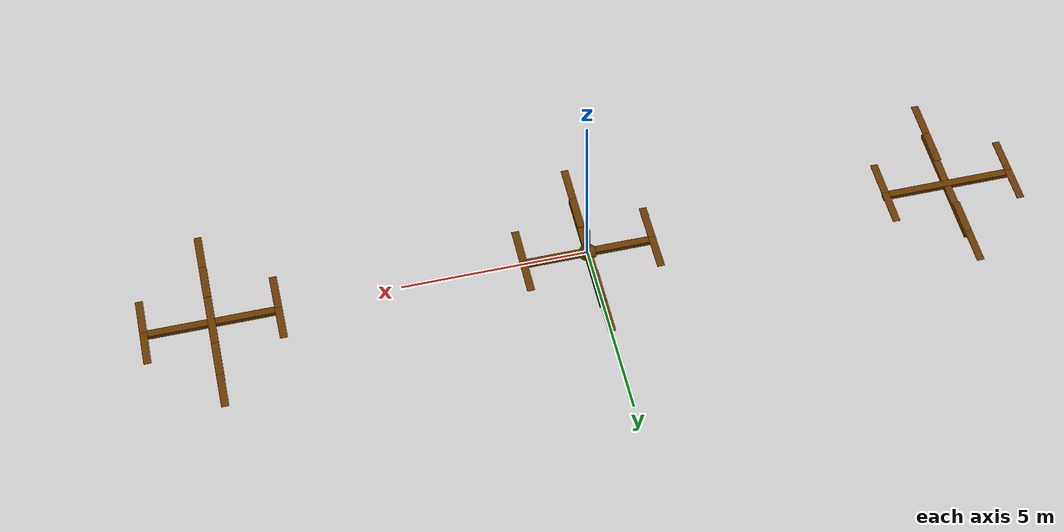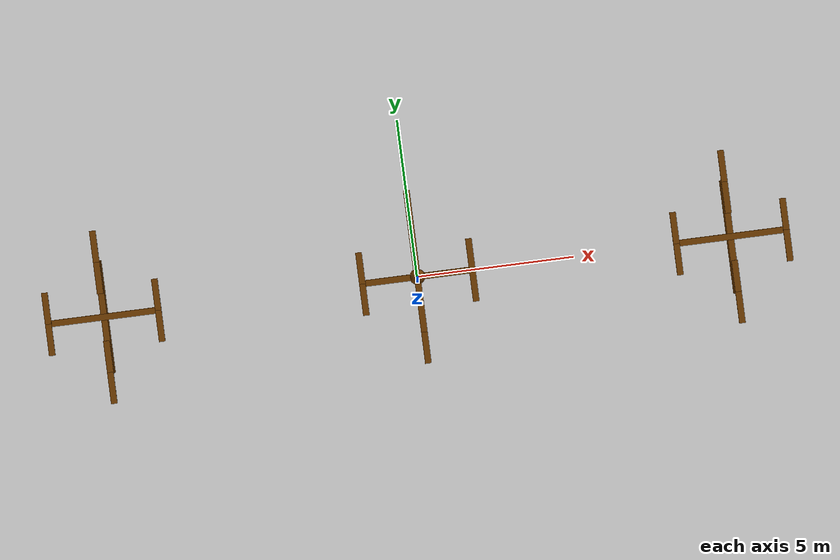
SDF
<?xml version="1.0" ?>
<sdf version="1.5">
  <world name="default">
    <physics type="ode">
      <gravity>0.0 0.0 -10.0</gravity>
      <ode>
        <solver>
          <type>quick</type>
          <iters>50</iters>
          <sor>0.8</sor>
        </solver>
        <constraints>
          <cfm>0.0</cfm>
          <erp>0.2</erp>
          <contact_max_correcting_vel>0.1</contact_max_correcting_vel>
          <contact_surface_layer>0.0</contact_surface_layer>
        </constraints>
      </ode>
      <real_time_factor>1</real_time_factor>
      <real_time_update_rate>0</real_time_update_rate>
      <max_step_size>0.001</max_step_size>
    </physics>
    <include>
      <uri>model://sun</uri>
    </include>

    <model name="ground_plane">
      <static>true</static>
      <link name="link">
        <collision name="collision">
          <geometry>
            <plane>
              <normal>0 0 1</normal>
              <size>1000 1000</size>
            </plane>
          </geometry>
          <surface>
            <friction>
              <ode>
                <mu>1</mu>
                <mu2>1</mu2>
              </ode>
            </friction>
          </surface>
        </collision>
        <visual name="visual">
          <cast_shadows>false</cast_shadows>
          <geometry>
            <plane>
              <normal>0 0 1</normal>
              <size>1000 1000</size>
            </plane>
          </geometry>
          <material>
            <script>
              <uri>file://media/materials/scripts/gazebo.material</uri>
              <name>Gazebo/Grey</name>
            </script>
          </material>
        </visual>
      </link>
    </model>

	<include>
		<uri>model://track_ball</uri>
		<pose>0 0 0 0 0 0</pose>
	</include>

	<include>
		<uri>model://quad_2292_1</uri>
		<pose>0 0 0 0 0 0</pose>
	</include>
	<include>
		<uri>model://quad_2292_2</uri>
		<pose>-10 0 0 0 0 0</pose>
	</include>
	<include>
		<uri>model://quad_2292_3</uri>
		<pose>10 0 0 0 0 0</pose>
	</include>
   </world>
</sdf>

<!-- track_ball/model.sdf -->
<sdf version="1.5">
	<model name="track_ball">
	  <pose>0 0 0.0 0 0 0</pose>
	  <static>false</static>

	  <link name="ball">
		<gravity>0</gravity>
		<pose>0 0 0 0 0 0</pose>
		<visual name="visual">
		  <geometry>
			<sphere>
			  <radius>0.25</radius>
			</sphere>
		  </geometry>
		  <material>
			<ambient>0.2 0.2 0.2 1.0</ambient>
			<diffuse>.421 0.225 0.0 1.0</diffuse>
		  </material>
		</visual>
	  </link>

	  <link name="x_axis">
		 <gravity>0</gravity>
		<pose>0.5 0 0 0 0 0</pose>
		<visual name="visual">
		  <geometry>
			<box>
			  <size>1 0.1 0.1</size>
			</box>
		  </geometry>
		  <material>
			<ambient>1.0 0.0 0.0 1.0</ambient>
			<diffuse>1.0 0.0 0.0 1.0</diffuse>
		  </material>
		</visual>
	  </link>

	  <link name="y_axis">
		<gravity>0</gravity>
		<pose>0 0.5 0 0 0 0</pose>
		<visual name="visual">
		  <geometry>
			<box>
			  <size>0.1 1 0.1</size>
			</box>
		  </geometry>
		  <material>
			<ambient>0.0 1.0 0.0 1.0</ambient>
			<diffuse>0.0 1.0 0.0 1.0</diffuse>
		  </material>
		</visual>
	  </link>

	  <link name="z_axis">
		<gravity>0</gravity>
		<pose>0 0 0.5 0 0 0</pose>
		<visual name="visual">
		  <geometry>
			<box>
			  <size>0.1 0.1 1</size>
			</box>
		  </geometry>
		  <material>
			<ambient>0.0 0.0 1.0 1.0</ambient>
			<diffuse>0.0 0.0 1.0 1.0</diffuse>
		  </material>
		</visual>
	  </link>

	  <joint name="x_joint" type="revolute">
		<parent>ball</parent>
		<child>x_axis</child>
		<pose>0.0 0.0 0.0 0.0 0.0 0.0</pose>
		<axis>
		  <limit>
			<lower>0</lower>
			<upper>0</upper>
		  </limit>
		  <xyz>1.0 0.0 0.0</xyz>
		</axis>
	  </joint>

	  <joint name="y_joint" type="revolute">
		<parent>ball</parent>
		<child>y_axis</child>
		<pose>0.0 0.0 0.0 0.0 0.0 0.0</pose>
		<axis>
		  <limit>
			<lower>0</lower>
			<upper>0</upper>
		  </limit>
		  <xyz>0.0 1.0 0.0</xyz>
		</axis>
	  </joint>

	  <joint name="z_joint" type="revolute">
		<parent>ball</parent>
		<child>z_axis</child>
		<pose>0.0 0.0 0.0 0.0 0.0 0.0</pose>
		<axis>
		  <limit>
			<lower>0</lower>
			<upper>0</upper>
		  </limit>
		  <xyz>0.0 0.0 1.0</xyz>
		</axis>
	  </joint>

	</model>
</sdf>

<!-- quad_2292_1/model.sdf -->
<sdf version="1.5">
	<model name="quad_2292_1">
	  <pose>0 0 0.1 0 0 0</pose>
	  <static>false</static>
	  <link name="body_1">
		<pose>0 0 0 0 0 0</pose>
		<inertial>
		  <pose>0.0 0.0 0.0 0.0 0.0 0.0</pose>
		  <inertia>
			<ixx>1.8</ixx>
			<ixy>0.0</ixy>
			<ixz>0.0</ixz>
			<iyy>10.8</iyy>
			<iyz>0.0</iyz>
			<izz>10.8</izz>
		  </inertia>
		  <mass>10.0</mass>
		</inertial>
		<collision name="collision">
		  <geometry>
			<box>
			  <size>3.6 0.2 0.2</size>
			</box>
		  </geometry>
		  <surface>
			<friction>
			  <ode>
				<mu>0.1</mu>
				<mu2>0.1</mu2>
			  </ode>
			</friction>
		  </surface>
		</collision>
		<visual name="visual">
		  <geometry>
			<box>
			  <size>3.6 0.2 0.2</size>
			</box>
		  </geometry>
		  <material>
			<ambient>0.2 0.2 0.2 1.0</ambient>
			<diffuse>.421 0.225 0.0 1.0</diffuse>
		  </material>
		</visual>
		<sensor name='imu_sensor' type='imu'>
		  <always_on>1</always_on>
		  <update_rate>1000</update_rate>
		  <imu>
			<noise>
			  <type>gaussian</type>
			  <rate>
				<mean>0</mean>
				<stddev>0.0002</stddev>
				<bias_mean>7.5e-06</bias_mean>
				<bias_stddev>8e-07</bias_stddev>
			  </rate>
			  <accel>
				<mean>0</mean>
				<stddev>0.017</stddev>
				<bias_mean>0.1</bias_mean>
				<bias_stddev>0.001</bias_stddev>
			  </accel>
			</noise>
		  </imu>
		  <pose>0 0 0 0 0 0</pose>
		</sensor>
	  </link>
	  <link name="body_2">
		<pose>0 0 0 0 0 0</pose>
		<inertial>
		  <pose>0.0 0.0 0.0 0.0 0.0 0.0</pose>
		  <inertia>
			<ixx>10.8</ixx>
			<ixy>0.0</ixy>
			<ixz>0.0</ixz>
			<iyy>1.8</iyy>
			<iyz>0.0</iyz>
			<izz>10.8</izz>
		  </inertia>
		  <mass>10.0</mass>
		</inertial>
		<collision name="collision">
		  <geometry>
			<box>
			  <size>0.2 3.6 0.2</size>
			</box>
		  </geometry>
		  <surface>
			<friction>
			  <ode>
				<mu>0.1</mu>
				<mu2>0.1</mu2>
			  </ode>
			</friction>
		  </surface>
		</collision>
		<visual name="visual">
		  <geometry>
			<box>
			  <size>0.2 3.6 0.2</size>
			</box>
		  </geometry>
		  <material>
			<ambient>0.2 0.2 0.2 1.0</ambient>
			<diffuse>.421 0.225 0.0 1.0</diffuse>
		  </material>
		</visual>
	  </link>
	  <joint name="body_joint" type="revolute">
		<parent>body_1</parent>
		<child>body_2</child>
		<pose>0.0 0.0 0.0 0.0 0.0 0.0</pose>
		<axis>
		  <limit>
			<lower>0</lower>
			<upper>0</upper>
		  </limit>
		  <xyz>0.0 0.0 1.0</xyz>
		  <dynamics>
			<damping>0.0001</damping>
		  </dynamics>
		</axis>
		<physics>
		  <ode>
			<cfm_damping>1</cfm_damping>
		  </ode>
		</physics>
	  </joint>

	<!-- Motor/Prop 1 -->
	  <link name="rod_1">
		<pose>-1.75 0 0.14 0 0 0</pose>
		<inertial>
		  <pose>0.0 0.0 0 0.0 0.0 0.0</pose>
		  <inertia>
			<ixx>0.012</ixx>
			<ixy>0.0</ixy>
			<ixz>0.0</ixz>
			<iyy>0.012</iyy>
			<iyz>0.0</iyz>
			<izz>0.0012</izz>
		  </inertia>
		  <mass>1.0</mass>
		</inertial>
		<collision name="collision">
		  <geometry>
			<box>
			  <size>0.02 0.02 0.08</size>
			</box>
		  </geometry>
		</collision>
		<visual name="visual">
		  <geometry>
			<box>
			  <size>0.02 0.02 0.08</size>
			</box>
		  </geometry>
		  <material>
			<ambient>0.3 0.3 0.3 1.0</ambient>
			<diffuse>.421 0.225 0.0 1.0</diffuse>
		  </material>
		</visual>
	  </link>
	  <link name="blade_1">
		<pose>-1.75 0 0.18 0 0 0</pose>
		<inertial>
		  <pose>0.0 0.25 0 0.0 0.0 0.0</pose>
		  <inertia>
			<ixx>0.0000465</ixx>
			<ixy>0.0</ixy>
			<ixz>0.0</ixz>
			<iyy>0.0000006</iyy>
			<iyz>0.0</iyz>
			<izz>0.0000470</izz>
		  </inertia>
		  <mass>0.01</mass>
		</inertial>
		<collision name="collision">
		  <pose>0.0 0.5 0 0.0 0.0 0.0</pose>
		  <geometry>
			<box>
			  <size>0.2 1.0 0.01</size>
			</box>
		  </geometry>
		</collision>
		<visual name="visual">
		  <pose>0.0 0.5 0 0.0 0.0 0.0</pose>
		  <geometry>
			<box>
			  <size>0.2 1.0 0.01</size>
			</box>
		  </geometry>
		  <material>
			<ambient>0.5 0.2 0.2 1.0</ambient>
			<diffuse>.421 0.225 0.0 1.0</diffuse>
		  </material>
		</visual>
	  </link>
	  <link name="blade_2">
		<pose>-1.75 0 0.18 0 0 3.141593</pose>
		<inertial>
		  <pose>0.0 0.25 0 0.0 0.0 0.0</pose>
		  <inertia>
			<ixx>0.0000465</ixx>
			<ixy>0.0</ixy>
			<ixz>0.0</ixz>
			<iyy>0.0000006</iyy>
			<iyz>0.0</iyz>
			<izz>0.0000470</izz>
		  </inertia>
		  <mass>0.01</mass>
		</inertial>
		<collision name="collision">
		  <pose>0.0 0.5 0 0.0 0.0 0.0</pose>
		  <geometry>
			<box>
			  <size>0.2 1.0 0.01</size>
			</box>
		  </geometry>
		</collision>
		<visual name="visual">
		  <pose>0.0 0.5 0 0.0 0.0 0</pose>
		  <geometry>
			<box>
			  <size>0.2 1.0 0.01</size>
			</box>
		  </geometry>
		  <material>
			<ambient>0.2 0.5 0.2 1.0</ambient>
			<diffuse>.421 0.225 0.0 1.0</diffuse>
		  </material>
		</visual>
	  </link>
	  <joint name="rod_1_joint" type="revolute">
		<parent>body_1</parent>
		<child>rod_1</child>
		<pose>0.0 0.0 0.0 0.0 0.0 0.0</pose>
		<axis>
		  <limit>
			<lower>-1e16</lower>
			<upper>1e16</upper>
		  </limit>
		  <xyz>0.0 0.0 -1.0</xyz>
		  <dynamics>
			<damping>0.0001</damping>
		  </dynamics>
		</axis>
		<physics>
		  <ode>
			<cfm_damping>1</cfm_damping>
		  </ode>
		</physics>
	  </joint>
	  <joint name="blade_1_joint" type="revolute">
		<parent>rod_1</parent>
		<child>blade_1</child>
		<pose>0.0 0.0 0.0 0.0 0.0 0.0</pose>
		<axis>
		  <limit>
			<lower>-0.0</lower>
			<upper>0.0</upper>
		  </limit>
		  <xyz>1.0 0.0 0.0</xyz>
		  <dynamics>
			<damping>1.000000</damping>
		  </dynamics>
		</axis>
		<physics>
		  <ode>
			<limit>
			  <cfm>0.004</cfm>
			  <erp>0.2</erp>
			</limit>
			<cfm_damping>1</cfm_damping>
		  </ode>
		</physics>
	  </joint>
	  <joint name="blade_2_joint" type="revolute">
		<parent>rod_1</parent>
		<child>blade_2</child>
		<pose>0.0 0.0 0.0 0.0 0.0 0.0</pose>
		<axis>
		  <limit>
			<lower>-0.0</lower>
			<upper>0.0</upper>
		  </limit>
		  <xyz>1.0 0.0 0.0</xyz>
		  <dynamics>
			<damping>1.000000</damping>
		  </dynamics>
		</axis>
		<physics>
		  <ode>
			<limit>
			  <cfm>0.004</cfm>
			  <erp>0.2</erp>
			</limit>
			<cfm_damping>1</cfm_damping>
		  </ode>
		</physics>
	  </joint>

	<!-- /Motor/Prop 1 -->

	<!-- Motor/Prop 2 -->
	  <link name="rod_2">
		<pose>1.75 0 0.14 0 0 0</pose>
		<inertial>
		  <pose>0.0 0.0 0 0.0 0.0 0.0</pose>
		  <inertia>
			<ixx>0.012</ixx>
			<ixy>0.0</ixy>
			<ixz>0.0</ixz>
			<iyy>0.012</iyy>
			<iyz>0.0</iyz>
			<izz>0.0012</izz>
		  </inertia>
		  <mass>1.0</mass>
		</inertial>
		<collision name="collision">
		  <geometry>
			<box>
			  <size>0.02 0.02 0.08</size>
			</box>
		  </geometry>
		</collision>
		<visual name="visual">
		  <geometry>
			<box>
			  <size>0.02 0.02 0.08</size>
			</box>
		  </geometry>
		  <material>
			<ambient>0.3 0.3 0.3 1.0</ambient>
			<diffuse>.421 0.225 0.0 1.0</diffuse>
		  </material>
		</visual>
	  </link>
	  <link name="blade_3">
		<pose>1.75 0 0.18 0 0 0</pose>
		<inertial>
		  <pose>0.0 0.25 0 0.0 0.0 0.0</pose>
		  <inertia>
			<ixx>0.0000465</ixx>
			<ixy>0.0</ixy>
			<ixz>0.0</ixz>
			<iyy>0.0000006</iyy>
			<iyz>0.0</iyz>
			<izz>0.0000470</izz>
		  </inertia>
		  <mass>0.01</mass>
		</inertial>
		<collision name="collision">
		  <pose>0.0 0.5 0 0.0 0.0 0.0</pose>
		  <geometry>
			<box>
			  <size>0.2 1.0 0.01</size>
			</box>
		  </geometry>
		</collision>
		<visual name="visual">
		  <pose>0.0 0.5 0 0.0 0.0 0.0</pose>
		  <geometry>
			<box>
			  <size>0.2 1.0 0.01</size>
			</box>
		  </geometry>
		  <material>
			<ambient>0.5 0.2 0.2 1.0</ambient>
			<diffuse>.421 0.225 0.0 1.0</diffuse>
		  </material>
		</visual>
	  </link>
	  <link name="blade_4">
		<pose>1.75 0 0.18 0 0 3.141593</pose>
		<inertial>
		  <pose>0.0 0.25 0 0.0 0.0 0.0</pose>
		  <inertia>
			<ixx>0.0000465</ixx>
			<ixy>0.0</ixy>
			<ixz>0.0</ixz>
			<iyy>0.0000006</iyy>
			<iyz>0.0</iyz>
			<izz>0.0000470</izz>
		  </inertia>
		  <mass>0.01</mass>
		</inertial>
		<collision name="collision">
		  <pose>0.0 0.5 0 0.0 0.0 0.0</pose>
		  <geometry>
			<box>
			  <size>0.2 1.0 0.01</size>
			</box>
		  </geometry>
		</collision>
		<visual name="visual">
		  <pose>0.0 0.5 0 0.0 0.0 0</pose>
		  <geometry>
			<box>
			  <size>0.2 1.0 0.01</size>
			</box>
		  </geometry>
		  <material>
			<ambient>0.2 0.5 0.2 1.0</ambient>
			<diffuse>.421 0.225 0.0 1.0</diffuse>
		  </material>
		</visual>
	  </link>
	  <joint name="rod_2_joint" type="revolute">
		<parent>body_1</parent>
		<child>rod_2</child>
		<pose>0.0 0.0 0.0 0.0 0.0 0.0</pose>
		<axis>
		  <limit>
			<lower>-1e16</lower>
			<upper>1e16</upper>
		  </limit>
		  <xyz>0.0 0.0 -1.0</xyz>
		  <dynamics>
			<damping>0.0001</damping>
		  </dynamics>
		</axis>
		<physics>
		  <ode>
			<cfm_damping>1</cfm_damping>
		  </ode>
		</physics>
	  </joint>
	  <joint name="blade_3_joint" type="revolute">
		<parent>rod_2</parent>
		<child>blade_3</child>
		<pose>0.0 0.0 0.0 0.0 0.0 0.0</pose>
		<axis>
		  <limit>
			<lower>-0.0</lower>
			<upper>0.0</upper>
		  </limit>
		  <xyz>1.0 0.0 0.0</xyz>
		  <dynamics>
			<damping>1.000000</damping>
		  </dynamics>
		</axis>
		<physics>
		  <ode>
			<limit>
			  <cfm>0.004</cfm>
			  <erp>0.2</erp>
			</limit>
			<cfm_damping>1</cfm_damping>
		  </ode>
		</physics>
	  </joint>
	  <joint name="blade_4_joint" type="revolute">
		<parent>rod_2</parent>
		<child>blade_4</child>
		<pose>0.0 0.0 0.0 0.0 0.0 0.0</pose>
		<axis>
		  <limit>
			<lower>-0.0</lower>
			<upper>0.0</upper>
		  </limit>
		  <xyz>1.0 0.0 0.0</xyz>
		  <dynamics>
			<damping>1.000000</damping>
		  </dynamics>
		</axis>
		<physics>
		  <ode>
			<limit>
			  <cfm>0.004</cfm>
			  <erp>0.2</erp>
			</limit>
			<cfm_damping>1</cfm_damping>
		  </ode>
		</physics>
	  </joint>
	<!-- /Motor/Prop 2 -->
	  <plugin name="quad_2292_1_blade_1" filename="libLiftDragPlugin.so">
		<a0>0.1</a0>
		<cla>0.100</cla>
		<cda>0.01</cda>
		<cma>0.00</cma>
		<alpha_stall>0.2</alpha_stall>
		<cla_stall>-0.2</cla_stall>
		<cda_stall>1.0</cda_stall>
		<cma_stall>0.0</cma_stall>
		<cp>0.0 0.5 0</cp>
		<area>0.2</area>
		<air_density>1.2041</air_density>
		<forward>1 0 0</forward>
		<upward>0 0 1</upward>
		<link_name>quad_2292_1::blade_1</link_name>
	  </plugin>
	  <plugin name="quad_2292_1_blade_2" filename="libLiftDragPlugin.so">
		<a0>0.1</a0>
		<cla>0.100</cla>
		<cda>0.01</cda>
		<cma>0.00</cma>
		<alpha_stall>0.2</alpha_stall>
		<cla_stall>-0.2</cla_stall>
		<cda_stall>1.0</cda_stall>
		<cma_stall>0.0</cma_stall>
		<cp>0.0 0.5 0</cp>
		<area>0.2</area>
		<air_density>1.2041</air_density>
		<forward>1 0 0</forward>
		<upward>0 0 1</upward>
		<link_name>quad_2292_1::blade_2</link_name>
	  </plugin>
	  <plugin name="quad_2292_1_blade_3" filename="libLiftDragPlugin.so">
		<a0>0.1</a0>
		<cla>0.100</cla>
		<cda>0.01</cda>
		<cma>0.00</cma>
		<alpha_stall>0.2</alpha_stall>
		<cla_stall>-0.2</cla_stall>
		<cda_stall>1.0</cda_stall>
		<cma_stall>0.0</cma_stall>
		<cp>0.0 0.5 0</cp>
		<area>0.2</area>
		<air_density>1.2041</air_density>
		<forward>1 0 0</forward>
		<upward>0 0 1</upward>
		<link_name>quad_2292_1::blade_3</link_name>
	  </plugin>
	  <plugin name="quad_2292_1_blade_4" filename="libLiftDragPlugin.so">
		<a0>0.1</a0>
		<cla>0.100</cla>
		<cda>0.01</cda>
		<cma>0.00</cma>
		<alpha_stall>0.2</alpha_stall>
		<cla_stall>-0.2</cla_stall>
		<cda_stall>1.0</cda_stall>
		<cma_stall>0.0</cma_stall>
		<cp>0.0 0.5 0</cp>
		<area>0.2</area>
		<air_density>1.2041</air_density>
		<forward>1 0 0</forward>
		<upward>0 0 1</upward>
		<link_name>quad_2292_1::blade_4</link_name>
	  </plugin>

	<!-- Motor/Prop 3 -->
	  <link name="rod_3">
		<pose>0 -1.75 0.14 0 0 0</pose>
		<inertial>
		  <pose>0.0 0.0 0 0.0 0.0 0.0</pose>
		  <inertia>
			<ixx>0.012</ixx>
			<ixy>0.0</ixy>
			<ixz>0.0</ixz>
			<iyy>0.012</iyy>
			<iyz>0.0</iyz>
			<izz>0.0012</izz>
		  </inertia>
		  <mass>1.0</mass>
		</inertial>
		<collision name="collision">
		  <geometry>
			<box>
			  <size>0.02 0.02 0.08</size>
			</box>
		  </geometry>
		</collision>
		<visual name="visual">
		  <geometry>
			<box>
			  <size>0.02 0.02 0.08</size>
			</box>
		  </geometry>
		  <material>
			<ambient>0.3 0.3 0.3 1.0</ambient>
			<diffuse>.421 0.225 0.0 1.0</diffuse>
		  </material>
		</visual>
	  </link>
	  <link name="blade_5">
		<pose>0 -1.75 0.18 0 0 0</pose>
		<inertial>
		  <pose>0.0 0.25 0 0.0 0.0 0.0</pose>
		  <inertia>
			<ixx>0.0000465</ixx>
			<ixy>0.0</ixy>
			<ixz>0.0</ixz>
			<iyy>0.0000006</iyy>
			<iyz>0.0</iyz>
			<izz>0.0000470</izz>
		  </inertia>
		  <mass>0.01</mass>
		</inertial>
		<collision name="collision">
		  <pose>0.0 0.5 0 0.0 0.0 0.0</pose>
		  <geometry>
			<box>
			  <size>0.2 1.0 0.01</size>
			</box>
		  </geometry>
		</collision>
		<visual name="visual">
		  <pose>0.0 0.5 0 0.0 0.0 0.0</pose>
		  <geometry>
			<box>
			  <size>0.2 1.0 0.01</size>
			</box>
		  </geometry>
		  <material>
			<ambient>0.5 0.2 0.2 1.0</ambient>
			<diffuse>.421 0.225 0.0 1.0</diffuse>
		  </material>
		</visual>
	  </link>
	  <link name="blade_6">
		<pose>0 -1.75 0.18 0 0 3.141593</pose>
		<inertial>
		  <pose>0.0 0.25 0 0.0 0.0 0.0</pose>
		  <inertia>
			<ixx>0.0000465</ixx>
			<ixy>0.0</ixy>
			<ixz>0.0</ixz>
			<iyy>0.0000006</iyy>
			<iyz>0.0</iyz>
			<izz>0.0000470</izz>
		  </inertia>
		  <mass>0.01</mass>
		</inertial>
		<collision name="collision">
		  <pose>0.0 0.5 0 0.0 0.0 0.0</pose>
		  <geometry>
			<box>
			  <size>0.2 1.0 0.01</size>
			</box>
		  </geometry>
		</collision>
		<visual name="visual">
		  <pose>0.0 0.5 0 0.0 0.0 0</pose>
		  <geometry>
			<box>
			  <size>0.2 1.0 0.01</size>
			</box>
		  </geometry>
		  <material>
			<ambient>0.2 0.5 0.2 1.0</ambient>
			<diffuse>.421 0.225 0.0 1.0</diffuse>
		  </material>
		</visual>
	  </link>
	  <joint name="rod_3_joint" type="revolute">
		<parent>body_2</parent>
		<child>rod_3</child>
		<pose>0.0 0.0 0.0 0.0 0.0 0.0</pose>
		<axis>
		  <limit>
			<lower>-1e16</lower>
			<upper>1e16</upper>
		  </limit>
		  <xyz>0.0 0.0 1.0</xyz>
		  <dynamics>
			<damping>0.0001</damping>
		  </dynamics>
		</axis>
		<physics>
		  <ode>
			<cfm_damping>1</cfm_damping>
		  </ode>
		</physics>
	  </joint>
	  <joint name="blade_5_joint" type="revolute">
		<parent>rod_3</parent>
		<child>blade_5</child>
		<pose>0.0 0.0 0.0 0.0 0.0 0.0</pose>
		<axis>
		  <limit>
			<lower>-0.0</lower>
			<upper>0.0</upper>
		  </limit>
		  <xyz>1.0 0.0 0.0</xyz>
		  <dynamics>
			<damping>1.000000</damping>
		  </dynamics>
		</axis>
		<physics>
		  <ode>
			<limit>
			  <cfm>0.004</cfm>
			  <erp>0.2</erp>
			</limit>
			<cfm_damping>1</cfm_damping>
		  </ode>
		</physics>
	  </joint>
	  <joint name="blade_6_joint" type="revolute">
		<parent>rod_3</parent>
		<child>blade_6</child>
		<pose>0.0 0.0 0.0 0.0 0.0 0.0</pose>
		<axis>
		  <limit>
			<lower>-0.0</lower>
			<upper>0.0</upper>
		  </limit>
		  <xyz>1.0 0.0 0.0</xyz>
		  <dynamics>
			<damping>1.000000</damping>
		  </dynamics>
		</axis>
		<physics>
		  <ode>
			<limit>
			  <cfm>0.004</cfm>
			  <erp>0.2</erp>
			</limit>
			<cfm_damping>1</cfm_damping>
		  </ode>
		</physics>
	  </joint>
	<!-- /Motor/Prop 3 -->

	<!-- Motor/Prop 4 -->
	  <link name="rod_4">
		<pose>0 1.75 0.14 0 0 0</pose>
		<inertial>
		  <pose>0.0 0.0 0 0.0 0.0 0.0</pose>
		  <inertia>
			<ixx>0.012</ixx>
			<ixy>0.0</ixy>
			<ixz>0.0</ixz>
			<iyy>0.012</iyy>
			<iyz>0.0</iyz>
			<izz>0.0012</izz>
		  </inertia>
		  <mass>1.0</mass>
		</inertial>
		<collision name="collision">
		  <geometry>
			<box>
			  <size>0.02 0.02 0.08</size>
			</box>
		  </geometry>
		</collision>
		<visual name="visual">
		  <geometry>
			<box>
			  <size>0.02 0.02 0.08</size>
			</box>
		  </geometry>
		  <material>
			<ambient>0.3 0.3 0.3 1.0</ambient>
			<diffuse>.421 0.225 0.0 1.0</diffuse>
		  </material>
		</visual>
	  </link>
	  <link name="blade_7">
		<pose>0 1.75 0.18 0 0 0</pose>
		<inertial>
		  <pose>0.0 0.25 0 0.0 0.0 0.0</pose>
		  <inertia>
			<ixx>0.0000465</ixx>
			<ixy>0.0</ixy>
			<ixz>0.0</ixz>
			<iyy>0.0000006</iyy>
			<iyz>0.0</iyz>
			<izz>0.0000470</izz>
		  </inertia>
		  <mass>0.01</mass>
		</inertial>
		<collision name="collision">
		  <pose>0.0 0.5 0 0.0 0.0 0.0</pose>
		  <geometry>
			<box>
			  <size>0.2 1.0 0.01</size>
			</box>
		  </geometry>
		</collision>
		<visual name="visual">
		  <pose>0.0 0.5 0 0.0 0.0 0.0</pose>
		  <geometry>
			<box>
			  <size>0.2 1.0 0.01</size>
			</box>
		  </geometry>
		  <material>
			<ambient>0.5 0.2 0.2 1.0</ambient>
			<diffuse>.421 0.225 0.0 1.0</diffuse>
		  </material>
		</visual>
	  </link>
	  <link name="blade_8">
		<pose>0 1.75 0.18 0 0 3.141593</pose>
		<inertial>
		  <pose>0.0 0.25 0 0.0 0.0 0.0</pose>
		  <inertia>
			<ixx>0.0000465</ixx>
			<ixy>0.0</ixy>
			<ixz>0.0</ixz>
			<iyy>0.0000006</iyy>
			<iyz>0.0</iyz>
			<izz>0.0000470</izz>
		  </inertia>
		  <mass>0.01</mass>
		</inertial>
		<collision name="collision">
		  <pose>0.0 0.5 0 0.0 0.0 0.0</pose>
		  <geometry>
			<box>
			  <size>0.2 1.0 0.01</size>
			</box>
		  </geometry>
		</collision>
		<visual name="visual">
		  <pose>0.0 0.5 0 0.0 0.0 0</pose>
		  <geometry>
			<box>
			  <size>0.2 1.0 0.01</size>
			</box>
		  </geometry>
		  <material>
			<ambient>0.2 0.5 0.2 1.0</ambient>
			<diffuse>.421 0.225 0.0 1.0</diffuse>
		  </material>
		</visual>
	  </link>
	  <joint name="rod_4_joint" type="revolute">
		<parent>body_2</parent>
		<child>rod_4</child>
		<pose>0.0 0.0 0.0 0.0 0.0 0.0</pose>
		<axis>
		  <limit>
			<lower>-1e16</lower>
			<upper>1e16</upper>
		  </limit>
		  <xyz>0.0 0.0 1.0</xyz>
		  <dynamics>
			<damping>0.0001</damping>
		  </dynamics>
		</axis>
		<physics>
		  <ode>
			<cfm_damping>1</cfm_damping>
		  </ode>
		</physics>
	  </joint>
	  <joint name="blade_7_joint" type="revolute">
		<parent>rod_4</parent>
		<child>blade_7</child>
		<pose>0.0 0.0 0.0 0.0 0.0 0.0</pose>
		<axis>
		  <limit>
			<lower>-0.0</lower>
			<upper>0.0</upper>
		  </limit>
		  <xyz>1.0 0.0 0.0</xyz>
		  <dynamics>
			<damping>1.000000</damping>
		  </dynamics>
		</axis>
		<physics>
		  <ode>
			<limit>
			  <cfm>0.004</cfm>
			  <erp>0.2</erp>
			</limit>
			<cfm_damping>1</cfm_damping>
		  </ode>
		</physics>
	  </joint>
	  <joint name="blade_8_joint" type="revolute">
		<parent>rod_4</parent>
		<child>blade_8</child>
		<pose>0.0 0.0 0.0 0.0 0.0 0.0</pose>
		<axis>
		  <limit>
			<lower>-0.0</lower>
			<upper>0.0</upper>
		  </limit>
		  <xyz>1.0 0.0 0.0</xyz>
		  <dynamics>
			<damping>1.000000</damping>
		  </dynamics>
		</axis>
		<physics>
		  <ode>
			<limit>
			  <cfm>0.004</cfm>
			  <erp>0.2</erp>
			</limit>
			<cfm_damping>1</cfm_damping>
		  </ode>
		</physics>
	  </joint>
	<!-- /Motor/Prop 4 -->
	  <plugin name="quad_2292_1_blade_5" filename="libLiftDragPlugin.so">
		<a0>0.1</a0>
		<cla>0.100</cla>
		<cda>0.01</cda>
		<cma>0.00</cma>
		<alpha_stall>0.2</alpha_stall>
		<cla_stall>-0.2</cla_stall>
		<cda_stall>1.0</cda_stall>
		<cma_stall>0.0</cma_stall>
		<cp>0.0 0.5 0</cp>
		<area>0.2</area>
		<air_density>1.2041</air_density>
		<forward>-1 0 0</forward>
		<upward>0 0 1</upward>
		<link_name>quad_2292_1::blade_5</link_name>
	  </plugin>
	  <plugin name="quad_2292_1_blade_6" filename="libLiftDragPlugin.so">
		<a0>0.1</a0>
		<cla>0.100</cla>
		<cda>0.01</cda>
		<cma>0.00</cma>
		<alpha_stall>0.2</alpha_stall>
		<cla_stall>-0.2</cla_stall>
		<cda_stall>1.0</cda_stall>
		<cma_stall>0.0</cma_stall>
		<cp>0.0 0.5 0</cp>
		<area>0.2</area>
		<air_density>1.2041</air_density>
		<forward>-1 0 0</forward>
		<upward>0 0 1</upward>
		<link_name>quad_2292_1::blade_6</link_name>
	  </plugin>
	  <plugin name="quad_2292_1_blade_7" filename="libLiftDragPlugin.so">
		<a0>0.1</a0>
		<cla>0.100</cla>
		<cda>0.01</cda>
		<cma>0.00</cma>
		<alpha_stall>0.2</alpha_stall>
		<cla_stall>-0.2</cla_stall>
		<cda_stall>1.0</cda_stall>
		<cma_stall>0.0</cma_stall>
		<cp>0.0 0.5 0</cp>
		<area>0.2</area>
		<air_density>1.2041</air_density>
		<forward>-1 0 0</forward>
		<upward>0 0 1</upward>
		<link_name>quad_2292_1::blade_7</link_name>
	  </plugin>
	  <plugin name="quad_2292_1_blade_8" filename="libLiftDragPlugin.so">
		<a0>0.1</a0>
		<cla>0.100</cla>
		<cda>0.01</cda>
		<cma>0.00</cma>
		<alpha_stall>0.2</alpha_stall>
		<cla_stall>-0.2</cla_stall>
		<cda_stall>1.0</cda_stall>
		<cma_stall>0.0</cma_stall>
		<cp>0.0 0.5 0</cp>
		<area>0.2</area>
		<air_density>1.2041</air_density>
		<forward>-1 0 0</forward>
		<upward>0 0 1</upward>
		<link_name>quad_2292_1::blade_8</link_name>
	  </plugin>

	</model>
</sdf>

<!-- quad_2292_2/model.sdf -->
<sdf version="1.5">
	<model name="quad_2292_2">
	  <pose>0 0 0.1 0 0 0</pose>
	  <static>false</static>
	  <link name="body_1">
		<pose>0 0 0 0 0 0</pose>
		<inertial>
		  <pose>0.0 0.0 0.0 0.0 0.0 0.0</pose>
		  <inertia>
			<ixx>1.8</ixx>
			<ixy>0.0</ixy>
			<ixz>0.0</ixz>
			<iyy>10.8</iyy>
			<iyz>0.0</iyz>
			<izz>10.8</izz>
		  </inertia>
		  <mass>10.0</mass>
		</inertial>
		<collision name="collision">
		  <geometry>
			<box>
			  <size>3.6 0.2 0.2</size>
			</box>
		  </geometry>
		  <surface>
			<friction>
			  <ode>
				<mu>0.1</mu>
				<mu2>0.1</mu2>
			  </ode>
			</friction>
		  </surface>
		</collision>
		<visual name="visual">
		  <geometry>
			<box>
			  <size>3.6 0.2 0.2</size>
			</box>
		  </geometry>
		  <material>
			<ambient>0.2 0.2 0.2 1.0</ambient>
			<diffuse>.421 0.225 0.0 1.0</diffuse>
		  </material>
		</visual>
		<sensor name='imu_sensor' type='imu'>
		  <always_on>1</always_on>
		  <update_rate>1000</update_rate>
		  <imu>
			<noise>
			  <type>gaussian</type>
			  <rate>
				<mean>0</mean>
				<stddev>0.0002</stddev>
				<bias_mean>7.5e-06</bias_mean>
				<bias_stddev>8e-07</bias_stddev>
			  </rate>
			  <accel>
				<mean>0</mean>
				<stddev>0.017</stddev>
				<bias_mean>0.1</bias_mean>
				<bias_stddev>0.001</bias_stddev>
			  </accel>
			</noise>
		  </imu>
		  <pose>0 0 0 0 0 0</pose>
		</sensor>
	  </link>
	  <link name="body_2">
		<pose>0 0 0 0 0 0</pose>
		<inertial>
		  <pose>0.0 0.0 0.0 0.0 0.0 0.0</pose>
		  <inertia>
			<ixx>10.8</ixx>
			<ixy>0.0</ixy>
			<ixz>0.0</ixz>
			<iyy>1.8</iyy>
			<iyz>0.0</iyz>
			<izz>10.8</izz>
		  </inertia>
		  <mass>10.0</mass>
		</inertial>
		<collision name="collision">
		  <geometry>
			<box>
			  <size>0.2 3.6 0.2</size>
			</box>
		  </geometry>
		  <surface>
			<friction>
			  <ode>
				<mu>0.1</mu>
				<mu2>0.1</mu2>
			  </ode>
			</friction>
		  </surface>
		</collision>
		<visual name="visual">
		  <geometry>
			<box>
			  <size>0.2 3.6 0.2</size>
			</box>
		  </geometry>
		  <material>
			<ambient>0.2 0.2 0.2 1.0</ambient>
			<diffuse>.421 0.225 0.0 1.0</diffuse>
		  </material>
		</visual>
	  </link>
	  <joint name="body_joint" type="revolute">
		<parent>body_1</parent>
		<child>body_2</child>
		<pose>0.0 0.0 0.0 0.0 0.0 0.0</pose>
		<axis>
		  <limit>
			<lower>0</lower>
			<upper>0</upper>
		  </limit>
		  <xyz>0.0 0.0 1.0</xyz>
		  <dynamics>
			<damping>0.0001</damping>
		  </dynamics>
		</axis>
		<physics>
		  <ode>
			<cfm_damping>1</cfm_damping>
		  </ode>
		</physics>
	  </joint>

	<!-- Motor/Prop 1 -->
	  <link name="rod_1">
		<pose>-1.75 0 0.14 0 0 0</pose>
		<inertial>
		  <pose>0.0 0.0 0 0.0 0.0 0.0</pose>
		  <inertia>
			<ixx>0.012</ixx>
			<ixy>0.0</ixy>
			<ixz>0.0</ixz>
			<iyy>0.012</iyy>
			<iyz>0.0</iyz>
			<izz>0.0012</izz>
		  </inertia>
		  <mass>1.0</mass>
		</inertial>
		<collision name="collision">
		  <geometry>
			<box>
			  <size>0.02 0.02 0.08</size>
			</box>
		  </geometry>
		</collision>
		<visual name="visual">
		  <geometry>
			<box>
			  <size>0.02 0.02 0.08</size>
			</box>
		  </geometry>
		  <material>
			<ambient>0.3 0.3 0.3 1.0</ambient>
			<diffuse>.421 0.225 0.0 1.0</diffuse>
		  </material>
		</visual>
	  </link>
	  <link name="blade_1">
		<pose>-1.75 0 0.18 0 0 0</pose>
		<inertial>
		  <pose>0.0 0.25 0 0.0 0.0 0.0</pose>
		  <inertia>
			<ixx>0.0000465</ixx>
			<ixy>0.0</ixy>
			<ixz>0.0</ixz>
			<iyy>0.0000006</iyy>
			<iyz>0.0</iyz>
			<izz>0.0000470</izz>
		  </inertia>
		  <mass>0.01</mass>
		</inertial>
		<collision name="collision">
		  <pose>0.0 0.5 0 0.0 0.0 0.0</pose>
		  <geometry>
			<box>
			  <size>0.2 1.0 0.01</size>
			</box>
		  </geometry>
		</collision>
		<visual name="visual">
		  <pose>0.0 0.5 0 0.0 0.0 0.0</pose>
		  <geometry>
			<box>
			  <size>0.2 1.0 0.01</size>
			</box>
		  </geometry>
		  <material>
			<ambient>0.5 0.2 0.2 1.0</ambient>
			<diffuse>.421 0.225 0.0 1.0</diffuse>
		  </material>
		</visual>
	  </link>
	  <link name="blade_2">
		<pose>-1.75 0 0.18 0 0 3.141593</pose>
		<inertial>
		  <pose>0.0 0.25 0 0.0 0.0 0.0</pose>
		  <inertia>
			<ixx>0.0000465</ixx>
			<ixy>0.0</ixy>
			<ixz>0.0</ixz>
			<iyy>0.0000006</iyy>
			<iyz>0.0</iyz>
			<izz>0.0000470</izz>
		  </inertia>
		  <mass>0.01</mass>
		</inertial>
		<collision name="collision">
		  <pose>0.0 0.5 0 0.0 0.0 0.0</pose>
		  <geometry>
			<box>
			  <size>0.2 1.0 0.01</size>
			</box>
		  </geometry>
		</collision>
		<visual name="visual">
		  <pose>0.0 0.5 0 0.0 0.0 0</pose>
		  <geometry>
			<box>
			  <size>0.2 1.0 0.01</size>
			</box>
		  </geometry>
		  <material>
			<ambient>0.2 0.5 0.2 1.0</ambient>
			<diffuse>.421 0.225 0.0 1.0</diffuse>
		  </material>
		</visual>
	  </link>
	  <joint name="rod_1_joint" type="revolute">
		<parent>body_1</parent>
		<child>rod_1</child>
		<pose>0.0 0.0 0.0 0.0 0.0 0.0</pose>
		<axis>
		  <limit>
			<lower>-1e16</lower>
			<upper>1e16</upper>
		  </limit>
		  <xyz>0.0 0.0 -1.0</xyz>
		  <dynamics>
			<damping>0.0001</damping>
		  </dynamics>
		</axis>
		<physics>
		  <ode>
			<cfm_damping>1</cfm_damping>
		  </ode>
		</physics>
	  </joint>
	  <joint name="blade_1_joint" type="revolute">
		<parent>rod_1</parent>
		<child>blade_1</child>
		<pose>0.0 0.0 0.0 0.0 0.0 0.0</pose>
		<axis>
		  <limit>
			<lower>-0.0</lower>
			<upper>0.0</upper>
		  </limit>
		  <xyz>1.0 0.0 0.0</xyz>
		  <dynamics>
			<damping>1.000000</damping>
		  </dynamics>
		</axis>
		<physics>
		  <ode>
			<limit>
			  <cfm>0.004</cfm>
			  <erp>0.2</erp>
			</limit>
			<cfm_damping>1</cfm_damping>
		  </ode>
		</physics>
	  </joint>
	  <joint name="blade_2_joint" type="revolute">
		<parent>rod_1</parent>
		<child>blade_2</child>
		<pose>0.0 0.0 0.0 0.0 0.0 0.0</pose>
		<axis>
		  <limit>
			<lower>-0.0</lower>
			<upper>0.0</upper>
		  </limit>
		  <xyz>1.0 0.0 0.0</xyz>
		  <dynamics>
			<damping>1.000000</damping>
		  </dynamics>
		</axis>
		<physics>
		  <ode>
			<limit>
			  <cfm>0.004</cfm>
			  <erp>0.2</erp>
			</limit>
			<cfm_damping>1</cfm_damping>
		  </ode>
		</physics>
	  </joint>

	<!-- /Motor/Prop 1 -->

	<!-- Motor/Prop 2 -->
	  <link name="rod_2">
		<pose>1.75 0 0.14 0 0 0</pose>
		<inertial>
		  <pose>0.0 0.0 0 0.0 0.0 0.0</pose>
		  <inertia>
			<ixx>0.012</ixx>
			<ixy>0.0</ixy>
			<ixz>0.0</ixz>
			<iyy>0.012</iyy>
			<iyz>0.0</iyz>
			<izz>0.0012</izz>
		  </inertia>
		  <mass>1.0</mass>
		</inertial>
		<collision name="collision">
		  <geometry>
			<box>
			  <size>0.02 0.02 0.08</size>
			</box>
		  </geometry>
		</collision>
		<visual name="visual">
		  <geometry>
			<box>
			  <size>0.02 0.02 0.08</size>
			</box>
		  </geometry>
		  <material>
			<ambient>0.3 0.3 0.3 1.0</ambient>
			<diffuse>.421 0.225 0.0 1.0</diffuse>
		  </material>
		</visual>
	  </link>
	  <link name="blade_3">
		<pose>1.75 0 0.18 0 0 0</pose>
		<inertial>
		  <pose>0.0 0.25 0 0.0 0.0 0.0</pose>
		  <inertia>
			<ixx>0.0000465</ixx>
			<ixy>0.0</ixy>
			<ixz>0.0</ixz>
			<iyy>0.0000006</iyy>
			<iyz>0.0</iyz>
			<izz>0.0000470</izz>
		  </inertia>
		  <mass>0.01</mass>
		</inertial>
		<collision name="collision">
		  <pose>0.0 0.5 0 0.0 0.0 0.0</pose>
		  <geometry>
			<box>
			  <size>0.2 1.0 0.01</size>
			</box>
		  </geometry>
		</collision>
		<visual name="visual">
		  <pose>0.0 0.5 0 0.0 0.0 0.0</pose>
		  <geometry>
			<box>
			  <size>0.2 1.0 0.01</size>
			</box>
		  </geometry>
		  <material>
			<ambient>0.5 0.2 0.2 1.0</ambient>
			<diffuse>.421 0.225 0.0 1.0</diffuse>
		  </material>
		</visual>
	  </link>
	  <link name="blade_4">
		<pose>1.75 0 0.18 0 0 3.141593</pose>
		<inertial>
		  <pose>0.0 0.25 0 0.0 0.0 0.0</pose>
		  <inertia>
			<ixx>0.0000465</ixx>
			<ixy>0.0</ixy>
			<ixz>0.0</ixz>
			<iyy>0.0000006</iyy>
			<iyz>0.0</iyz>
			<izz>0.0000470</izz>
		  </inertia>
		  <mass>0.01</mass>
		</inertial>
		<collision name="collision">
		  <pose>0.0 0.5 0 0.0 0.0 0.0</pose>
		  <geometry>
			<box>
			  <size>0.2 1.0 0.01</size>
			</box>
		  </geometry>
		</collision>
		<visual name="visual">
		  <pose>0.0 0.5 0 0.0 0.0 0</pose>
		  <geometry>
			<box>
			  <size>0.2 1.0 0.01</size>
			</box>
		  </geometry>
		  <material>
			<ambient>0.2 0.5 0.2 1.0</ambient>
			<diffuse>.421 0.225 0.0 1.0</diffuse>
		  </material>
		</visual>
	  </link>
	  <joint name="rod_2_joint" type="revolute">
		<parent>body_1</parent>
		<child>rod_2</child>
		<pose>0.0 0.0 0.0 0.0 0.0 0.0</pose>
		<axis>
		  <limit>
			<lower>-1e16</lower>
			<upper>1e16</upper>
		  </limit>
		  <xyz>0.0 0.0 -1.0</xyz>
		  <dynamics>
			<damping>0.0001</damping>
		  </dynamics>
		</axis>
		<physics>
		  <ode>
			<cfm_damping>1</cfm_damping>
		  </ode>
		</physics>
	  </joint>
	  <joint name="blade_3_joint" type="revolute">
		<parent>rod_2</parent>
		<child>blade_3</child>
		<pose>0.0 0.0 0.0 0.0 0.0 0.0</pose>
		<axis>
		  <limit>
			<lower>-0.0</lower>
			<upper>0.0</upper>
		  </limit>
		  <xyz>1.0 0.0 0.0</xyz>
		  <dynamics>
			<damping>1.000000</damping>
		  </dynamics>
		</axis>
		<physics>
		  <ode>
			<limit>
			  <cfm>0.004</cfm>
			  <erp>0.2</erp>
			</limit>
			<cfm_damping>1</cfm_damping>
		  </ode>
		</physics>
	  </joint>
	  <joint name="blade_4_joint" type="revolute">
		<parent>rod_2</parent>
		<child>blade_4</child>
		<pose>0.0 0.0 0.0 0.0 0.0 0.0</pose>
		<axis>
		  <limit>
			<lower>-0.0</lower>
			<upper>0.0</upper>
		  </limit>
		  <xyz>1.0 0.0 0.0</xyz>
		  <dynamics>
			<damping>1.000000</damping>
		  </dynamics>
		</axis>
		<physics>
		  <ode>
			<limit>
			  <cfm>0.004</cfm>
			  <erp>0.2</erp>
			</limit>
			<cfm_damping>1</cfm_damping>
		  </ode>
		</physics>
	  </joint>
	<!-- /Motor/Prop 2 -->
	  <plugin name="quad_2292_2_blade_1" filename="libLiftDragPlugin.so">
		<a0>0.1</a0>
		<cla>0.100</cla>
		<cda>0.01</cda>
		<cma>0.00</cma>
		<alpha_stall>0.2</alpha_stall>
		<cla_stall>-0.2</cla_stall>
		<cda_stall>1.0</cda_stall>
		<cma_stall>0.0</cma_stall>
		<cp>0.0 0.5 0</cp>
		<area>0.2</area>
		<air_density>1.2041</air_density>
		<forward>1 0 0</forward>
		<upward>0 0 1</upward>
		<link_name>quad_2292_2::blade_1</link_name>
	  </plugin>
	  <plugin name="quad_2292_2_blade_2" filename="libLiftDragPlugin.so">
		<a0>0.1</a0>
		<cla>0.100</cla>
		<cda>0.01</cda>
		<cma>0.00</cma>
		<alpha_stall>0.2</alpha_stall>
		<cla_stall>-0.2</cla_stall>
		<cda_stall>1.0</cda_stall>
		<cma_stall>0.0</cma_stall>
		<cp>0.0 0.5 0</cp>
		<area>0.2</area>
		<air_density>1.2041</air_density>
		<forward>1 0 0</forward>
		<upward>0 0 1</upward>
		<link_name>quad_2292_2::blade_2</link_name>
	  </plugin>
	  <plugin name="quad_2292_2_blade_3" filename="libLiftDragPlugin.so">
		<a0>0.1</a0>
		<cla>0.100</cla>
		<cda>0.01</cda>
		<cma>0.00</cma>
		<alpha_stall>0.2</alpha_stall>
		<cla_stall>-0.2</cla_stall>
		<cda_stall>1.0</cda_stall>
		<cma_stall>0.0</cma_stall>
		<cp>0.0 0.5 0</cp>
		<area>0.2</area>
		<air_density>1.2041</air_density>
		<forward>1 0 0</forward>
		<upward>0 0 1</upward>
		<link_name>quad_2292_2::blade_3</link_name>
	  </plugin>
	  <plugin name="quad_2292_2_blade_4" filename="libLiftDragPlugin.so">
		<a0>0.1</a0>
		<cla>0.100</cla>
		<cda>0.01</cda>
		<cma>0.00</cma>
		<alpha_stall>0.2</alpha_stall>
		<cla_stall>-0.2</cla_stall>
		<cda_stall>1.0</cda_stall>
		<cma_stall>0.0</cma_stall>
		<cp>0.0 0.5 0</cp>
		<area>0.2</area>
		<air_density>1.2041</air_density>
		<forward>1 0 0</forward>
		<upward>0 0 1</upward>
		<link_name>quad_2292_2::blade_4</link_name>
	  </plugin>

	<!-- Motor/Prop 3 -->
	  <link name="rod_3">
		<pose>0 -1.75 0.14 0 0 0</pose>
		<inertial>
		  <pose>0.0 0.0 0 0.0 0.0 0.0</pose>
		  <inertia>
			<ixx>0.012</ixx>
			<ixy>0.0</ixy>
			<ixz>0.0</ixz>
			<iyy>0.012</iyy>
			<iyz>0.0</iyz>
			<izz>0.0012</izz>
		  </inertia>
		  <mass>1.0</mass>
		</inertial>
		<collision name="collision">
		  <geometry>
			<box>
			  <size>0.02 0.02 0.08</size>
			</box>
		  </geometry>
		</collision>
		<visual name="visual">
		  <geometry>
			<box>
			  <size>0.02 0.02 0.08</size>
			</box>
		  </geometry>
		  <material>
			<ambient>0.3 0.3 0.3 1.0</ambient>
			<diffuse>.421 0.225 0.0 1.0</diffuse>
		  </material>
		</visual>
	  </link>
	  <link name="blade_5">
		<pose>0 -1.75 0.18 0 0 0</pose>
		<inertial>
		  <pose>0.0 0.25 0 0.0 0.0 0.0</pose>
		  <inertia>
			<ixx>0.0000465</ixx>
			<ixy>0.0</ixy>
			<ixz>0.0</ixz>
			<iyy>0.0000006</iyy>
			<iyz>0.0</iyz>
			<izz>0.0000470</izz>
		  </inertia>
		  <mass>0.01</mass>
		</inertial>
		<collision name="collision">
		  <pose>0.0 0.5 0 0.0 0.0 0.0</pose>
		  <geometry>
			<box>
			  <size>0.2 1.0 0.01</size>
			</box>
		  </geometry>
		</collision>
		<visual name="visual">
		  <pose>0.0 0.5 0 0.0 0.0 0.0</pose>
		  <geometry>
			<box>
			  <size>0.2 1.0 0.01</size>
			</box>
		  </geometry>
		  <material>
			<ambient>0.5 0.2 0.2 1.0</ambient>
			<diffuse>.421 0.225 0.0 1.0</diffuse>
		  </material>
		</visual>
	  </link>
	  <link name="blade_6">
		<pose>0 -1.75 0.18 0 0 3.141593</pose>
		<inertial>
		  <pose>0.0 0.25 0 0.0 0.0 0.0</pose>
		  <inertia>
			<ixx>0.0000465</ixx>
			<ixy>0.0</ixy>
			<ixz>0.0</ixz>
			<iyy>0.0000006</iyy>
			<iyz>0.0</iyz>
			<izz>0.0000470</izz>
		  </inertia>
		  <mass>0.01</mass>
		</inertial>
		<collision name="collision">
		  <pose>0.0 0.5 0 0.0 0.0 0.0</pose>
		  <geometry>
			<box>
			  <size>0.2 1.0 0.01</size>
			</box>
		  </geometry>
		</collision>
		<visual name="visual">
		  <pose>0.0 0.5 0 0.0 0.0 0</pose>
		  <geometry>
			<box>
			  <size>0.2 1.0 0.01</size>
			</box>
		  </geometry>
		  <material>
			<ambient>0.2 0.5 0.2 1.0</ambient>
			<diffuse>.421 0.225 0.0 1.0</diffuse>
		  </material>
		</visual>
	  </link>
	  <joint name="rod_3_joint" type="revolute">
		<parent>body_2</parent>
		<child>rod_3</child>
		<pose>0.0 0.0 0.0 0.0 0.0 0.0</pose>
		<axis>
		  <limit>
			<lower>-1e16</lower>
			<upper>1e16</upper>
		  </limit>
		  <xyz>0.0 0.0 1.0</xyz>
		  <dynamics>
			<damping>0.0001</damping>
		  </dynamics>
		</axis>
		<physics>
		  <ode>
			<cfm_damping>1</cfm_damping>
		  </ode>
		</physics>
	  </joint>
	  <joint name="blade_5_joint" type="revolute">
		<parent>rod_3</parent>
		<child>blade_5</child>
		<pose>0.0 0.0 0.0 0.0 0.0 0.0</pose>
		<axis>
		  <limit>
			<lower>-0.0</lower>
			<upper>0.0</upper>
		  </limit>
		  <xyz>1.0 0.0 0.0</xyz>
		  <dynamics>
			<damping>1.000000</damping>
		  </dynamics>
		</axis>
		<physics>
		  <ode>
			<limit>
			  <cfm>0.004</cfm>
			  <erp>0.2</erp>
			</limit>
			<cfm_damping>1</cfm_damping>
		  </ode>
		</physics>
	  </joint>
	  <joint name="blade_6_joint" type="revolute">
		<parent>rod_3</parent>
		<child>blade_6</child>
		<pose>0.0 0.0 0.0 0.0 0.0 0.0</pose>
		<axis>
		  <limit>
			<lower>-0.0</lower>
			<upper>0.0</upper>
		  </limit>
		  <xyz>1.0 0.0 0.0</xyz>
		  <dynamics>
			<damping>1.000000</damping>
		  </dynamics>
		</axis>
		<physics>
		  <ode>
			<limit>
			  <cfm>0.004</cfm>
			  <erp>0.2</erp>
			</limit>
			<cfm_damping>1</cfm_damping>
		  </ode>
		</physics>
	  </joint>
	<!-- /Motor/Prop 3 -->

	<!-- Motor/Prop 4 -->
	  <link name="rod_4">
		<pose>0 1.75 0.14 0 0 0</pose>
		<inertial>
		  <pose>0.0 0.0 0 0.0 0.0 0.0</pose>
		  <inertia>
			<ixx>0.012</ixx>
			<ixy>0.0</ixy>
			<ixz>0.0</ixz>
			<iyy>0.012</iyy>
			<iyz>0.0</iyz>
			<izz>0.0012</izz>
		  </inertia>
		  <mass>1.0</mass>
		</inertial>
		<collision name="collision">
		  <geometry>
			<box>
			  <size>0.02 0.02 0.08</size>
			</box>
		  </geometry>
		</collision>
		<visual name="visual">
		  <geometry>
			<box>
			  <size>0.02 0.02 0.08</size>
			</box>
		  </geometry>
		  <material>
			<ambient>0.3 0.3 0.3 1.0</ambient>
			<diffuse>.421 0.225 0.0 1.0</diffuse>
		  </material>
		</visual>
	  </link>
	  <link name="blade_7">
		<pose>0 1.75 0.18 0 0 0</pose>
		<inertial>
		  <pose>0.0 0.25 0 0.0 0.0 0.0</pose>
		  <inertia>
			<ixx>0.0000465</ixx>
			<ixy>0.0</ixy>
			<ixz>0.0</ixz>
			<iyy>0.0000006</iyy>
			<iyz>0.0</iyz>
			<izz>0.0000470</izz>
		  </inertia>
		  <mass>0.01</mass>
		</inertial>
		<collision name="collision">
		  <pose>0.0 0.5 0 0.0 0.0 0.0</pose>
		  <geometry>
			<box>
			  <size>0.2 1.0 0.01</size>
			</box>
		  </geometry>
		</collision>
		<visual name="visual">
		  <pose>0.0 0.5 0 0.0 0.0 0.0</pose>
		  <geometry>
			<box>
			  <size>0.2 1.0 0.01</size>
			</box>
		  </geometry>
		  <material>
			<ambient>0.5 0.2 0.2 1.0</ambient>
			<diffuse>.421 0.225 0.0 1.0</diffuse>
		  </material>
		</visual>
	  </link>
	  <link name="blade_8">
		<pose>0 1.75 0.18 0 0 3.141593</pose>
		<inertial>
		  <pose>0.0 0.25 0 0.0 0.0 0.0</pose>
		  <inertia>
			<ixx>0.0000465</ixx>
			<ixy>0.0</ixy>
			<ixz>0.0</ixz>
			<iyy>0.0000006</iyy>
			<iyz>0.0</iyz>
			<izz>0.0000470</izz>
		  </inertia>
		  <mass>0.01</mass>
		</inertial>
		<collision name="collision">
		  <pose>0.0 0.5 0 0.0 0.0 0.0</pose>
		  <geometry>
			<box>
			  <size>0.2 1.0 0.01</size>
			</box>
		  </geometry>
		</collision>
		<visual name="visual">
		  <pose>0.0 0.5 0 0.0 0.0 0</pose>
		  <geometry>
			<box>
			  <size>0.2 1.0 0.01</size>
			</box>
		  </geometry>
		  <material>
			<ambient>0.2 0.5 0.2 1.0</ambient>
			<diffuse>.421 0.225 0.0 1.0</diffuse>
		  </material>
		</visual>
	  </link>
	  <joint name="rod_4_joint" type="revolute">
		<parent>body_2</parent>
		<child>rod_4</child>
		<pose>0.0 0.0 0.0 0.0 0.0 0.0</pose>
		<axis>
		  <limit>
			<lower>-1e16</lower>
			<upper>1e16</upper>
		  </limit>
		  <xyz>0.0 0.0 1.0</xyz>
		  <dynamics>
			<damping>0.0001</damping>
		  </dynamics>
		</axis>
		<physics>
		  <ode>
			<cfm_damping>1</cfm_damping>
		  </ode>
		</physics>
	  </joint>
	  <joint name="blade_7_joint" type="revolute">
		<parent>rod_4</parent>
		<child>blade_7</child>
		<pose>0.0 0.0 0.0 0.0 0.0 0.0</pose>
		<axis>
		  <limit>
			<lower>-0.0</lower>
			<upper>0.0</upper>
		  </limit>
		  <xyz>1.0 0.0 0.0</xyz>
		  <dynamics>
			<damping>1.000000</damping>
		  </dynamics>
		</axis>
		<physics>
		  <ode>
			<limit>
			  <cfm>0.004</cfm>
			  <erp>0.2</erp>
			</limit>
			<cfm_damping>1</cfm_damping>
		  </ode>
		</physics>
	  </joint>
	  <joint name="blade_8_joint" type="revolute">
		<parent>rod_4</parent>
		<child>blade_8</child>
		<pose>0.0 0.0 0.0 0.0 0.0 0.0</pose>
		<axis>
		  <limit>
			<lower>-0.0</lower>
			<upper>0.0</upper>
		  </limit>
		  <xyz>1.0 0.0 0.0</xyz>
		  <dynamics>
			<damping>1.000000</damping>
		  </dynamics>
		</axis>
		<physics>
		  <ode>
			<limit>
			  <cfm>0.004</cfm>
			  <erp>0.2</erp>
			</limit>
			<cfm_damping>1</cfm_damping>
		  </ode>
		</physics>
	  </joint>
	<!-- /Motor/Prop 4 -->
	  <plugin name="quad_2292_2_blade_5" filename="libLiftDragPlugin.so">
		<a0>0.1</a0>
		<cla>0.100</cla>
		<cda>0.01</cda>
		<cma>0.00</cma>
		<alpha_stall>0.2</alpha_stall>
		<cla_stall>-0.2</cla_stall>
		<cda_stall>1.0</cda_stall>
		<cma_stall>0.0</cma_stall>
		<cp>0.0 0.5 0</cp>
		<area>0.2</area>
		<air_density>1.2041</air_density>
		<forward>-1 0 0</forward>
		<upward>0 0 1</upward>
		<link_name>quad_2292_2::blade_5</link_name>
	  </plugin>
	  <plugin name="quad_2292_2_blade_6" filename="libLiftDragPlugin.so">
		<a0>0.1</a0>
		<cla>0.100</cla>
		<cda>0.01</cda>
		<cma>0.00</cma>
		<alpha_stall>0.2</alpha_stall>
		<cla_stall>-0.2</cla_stall>
		<cda_stall>1.0</cda_stall>
		<cma_stall>0.0</cma_stall>
		<cp>0.0 0.5 0</cp>
		<area>0.2</area>
		<air_density>1.2041</air_density>
		<forward>-1 0 0</forward>
		<upward>0 0 1</upward>
		<link_name>quad_2292_2::blade_6</link_name>
	  </plugin>
	  <plugin name="quad_2292_2_blade_7" filename="libLiftDragPlugin.so">
		<a0>0.1</a0>
		<cla>0.100</cla>
		<cda>0.01</cda>
		<cma>0.00</cma>
		<alpha_stall>0.2</alpha_stall>
		<cla_stall>-0.2</cla_stall>
		<cda_stall>1.0</cda_stall>
		<cma_stall>0.0</cma_stall>
		<cp>0.0 0.5 0</cp>
		<area>0.2</area>
		<air_density>1.2041</air_density>
		<forward>-1 0 0</forward>
		<upward>0 0 1</upward>
		<link_name>quad_2292_2::blade_7</link_name>
	  </plugin>
	  <plugin name="quad_2292_2_blade_8" filename="libLiftDragPlugin.so">
		<a0>0.1</a0>
		<cla>0.100</cla>
		<cda>0.01</cda>
		<cma>0.00</cma>
		<alpha_stall>0.2</alpha_stall>
		<cla_stall>-0.2</cla_stall>
		<cda_stall>1.0</cda_stall>
		<cma_stall>0.0</cma_stall>
		<cp>0.0 0.5 0</cp>
		<area>0.2</area>
		<air_density>1.2041</air_density>
		<forward>-1 0 0</forward>
		<upward>0 0 1</upward>
		<link_name>quad_2292_2::blade_8</link_name>
	  </plugin>

	</model>
</sdf>

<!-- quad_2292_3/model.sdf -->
<sdf version="1.5">
	<model name="quad_2292_3">
	  <pose>0 0 0.1 0 0 0</pose>
	  <static>false</static>
	  <link name="body_1">
		<pose>0 0 0 0 0 0</pose>
		<inertial>
		  <pose>0.0 0.0 0.0 0.0 0.0 0.0</pose>
		  <inertia>
			<ixx>1.8</ixx>
			<ixy>0.0</ixy>
			<ixz>0.0</ixz>
			<iyy>10.8</iyy>
			<iyz>0.0</iyz>
			<izz>10.8</izz>
		  </inertia>
		  <mass>10.0</mass>
		</inertial>
		<collision name="collision">
		  <geometry>
			<box>
			  <size>3.6 0.2 0.2</size>
			</box>
		  </geometry>
		  <surface>
			<friction>
			  <ode>
				<mu>0.1</mu>
				<mu2>0.1</mu2>
			  </ode>
			</friction>
		  </surface>
		</collision>
		<visual name="visual">
		  <geometry>
			<box>
			  <size>3.6 0.2 0.2</size>
			</box>
		  </geometry>
		  <material>
			<ambient>0.2 0.2 0.2 1.0</ambient>
			<diffuse>.421 0.225 0.0 1.0</diffuse>
		  </material>
		</visual>
		<sensor name='imu_sensor' type='imu'>
		  <always_on>1</always_on>
		  <update_rate>1000</update_rate>
		  <imu>
			<noise>
			  <type>gaussian</type>
			  <rate>
				<mean>0</mean>
				<stddev>0.0002</stddev>
				<bias_mean>7.5e-06</bias_mean>
				<bias_stddev>8e-07</bias_stddev>
			  </rate>
			  <accel>
				<mean>0</mean>
				<stddev>0.017</stddev>
				<bias_mean>0.1</bias_mean>
				<bias_stddev>0.001</bias_stddev>
			  </accel>
			</noise>
		  </imu>
		  <pose>0 0 0 0 0 0</pose>
		</sensor>
	  </link>
	  <link name="body_2">
		<pose>0 0 0 0 0 0</pose>
		<inertial>
		  <pose>0.0 0.0 0.0 0.0 0.0 0.0</pose>
		  <inertia>
			<ixx>10.8</ixx>
			<ixy>0.0</ixy>
			<ixz>0.0</ixz>
			<iyy>1.8</iyy>
			<iyz>0.0</iyz>
			<izz>10.8</izz>
		  </inertia>
		  <mass>10.0</mass>
		</inertial>
		<collision name="collision">
		  <geometry>
			<box>
			  <size>0.2 3.6 0.2</size>
			</box>
		  </geometry>
		  <surface>
			<friction>
			  <ode>
				<mu>0.1</mu>
				<mu2>0.1</mu2>
			  </ode>
			</friction>
		  </surface>
		</collision>
		<visual name="visual">
		  <geometry>
			<box>
			  <size>0.2 3.6 0.2</size>
			</box>
		  </geometry>
		  <material>
			<ambient>0.2 0.2 0.2 1.0</ambient>
			<diffuse>.421 0.225 0.0 1.0</diffuse>
		  </material>
		</visual>
	  </link>
	  <joint name="body_joint" type="revolute">
		<parent>body_1</parent>
		<child>body_2</child>
		<pose>0.0 0.0 0.0 0.0 0.0 0.0</pose>
		<axis>
		  <limit>
			<lower>0</lower>
			<upper>0</upper>
		  </limit>
		  <xyz>0.0 0.0 1.0</xyz>
		  <dynamics>
			<damping>0.0001</damping>
		  </dynamics>
		</axis>
		<physics>
		  <ode>
			<cfm_damping>1</cfm_damping>
		  </ode>
		</physics>
	  </joint>

	<!-- Motor/Prop 1 -->
	  <link name="rod_1">
		<pose>-1.75 0 0.14 0 0 0</pose>
		<inertial>
		  <pose>0.0 0.0 0 0.0 0.0 0.0</pose>
		  <inertia>
			<ixx>0.012</ixx>
			<ixy>0.0</ixy>
			<ixz>0.0</ixz>
			<iyy>0.012</iyy>
			<iyz>0.0</iyz>
			<izz>0.0012</izz>
		  </inertia>
		  <mass>1.0</mass>
		</inertial>
		<collision name="collision">
		  <geometry>
			<box>
			  <size>0.02 0.02 0.08</size>
			</box>
		  </geometry>
		</collision>
		<visual name="visual">
		  <geometry>
			<box>
			  <size>0.02 0.02 0.08</size>
			</box>
		  </geometry>
		  <material>
			<ambient>0.3 0.3 0.3 1.0</ambient>
			<diffuse>.421 0.225 0.0 1.0</diffuse>
		  </material>
		</visual>
	  </link>
	  <link name="blade_1">
		<pose>-1.75 0 0.18 0 0 0</pose>
		<inertial>
		  <pose>0.0 0.25 0 0.0 0.0 0.0</pose>
		  <inertia>
			<ixx>0.0000465</ixx>
			<ixy>0.0</ixy>
			<ixz>0.0</ixz>
			<iyy>0.0000006</iyy>
			<iyz>0.0</iyz>
			<izz>0.0000470</izz>
		  </inertia>
		  <mass>0.01</mass>
		</inertial>
		<collision name="collision">
		  <pose>0.0 0.5 0 0.0 0.0 0.0</pose>
		  <geometry>
			<box>
			  <size>0.2 1.0 0.01</size>
			</box>
		  </geometry>
		</collision>
		<visual name="visual">
		  <pose>0.0 0.5 0 0.0 0.0 0.0</pose>
		  <geometry>
			<box>
			  <size>0.2 1.0 0.01</size>
			</box>
		  </geometry>
		  <material>
			<ambient>0.5 0.2 0.2 1.0</ambient>
			<diffuse>.421 0.225 0.0 1.0</diffuse>
		  </material>
		</visual>
	  </link>
	  <link name="blade_2">
		<pose>-1.75 0 0.18 0 0 3.141593</pose>
		<inertial>
		  <pose>0.0 0.25 0 0.0 0.0 0.0</pose>
		  <inertia>
			<ixx>0.0000465</ixx>
			<ixy>0.0</ixy>
			<ixz>0.0</ixz>
			<iyy>0.0000006</iyy>
			<iyz>0.0</iyz>
			<izz>0.0000470</izz>
		  </inertia>
		  <mass>0.01</mass>
		</inertial>
		<collision name="collision">
		  <pose>0.0 0.5 0 0.0 0.0 0.0</pose>
		  <geometry>
			<box>
			  <size>0.2 1.0 0.01</size>
			</box>
		  </geometry>
		</collision>
		<visual name="visual">
		  <pose>0.0 0.5 0 0.0 0.0 0</pose>
		  <geometry>
			<box>
			  <size>0.2 1.0 0.01</size>
			</box>
		  </geometry>
		  <material>
			<ambient>0.2 0.5 0.2 1.0</ambient>
			<diffuse>.421 0.225 0.0 1.0</diffuse>
		  </material>
		</visual>
	  </link>
	  <joint name="rod_1_joint" type="revolute">
		<parent>body_1</parent>
		<child>rod_1</child>
		<pose>0.0 0.0 0.0 0.0 0.0 0.0</pose>
		<axis>
		  <limit>
			<lower>-1e16</lower>
			<upper>1e16</upper>
		  </limit>
		  <xyz>0.0 0.0 -1.0</xyz>
		  <dynamics>
			<damping>0.0001</damping>
		  </dynamics>
		</axis>
		<physics>
		  <ode>
			<cfm_damping>1</cfm_damping>
		  </ode>
		</physics>
	  </joint>
	  <joint name="blade_1_joint" type="revolute">
		<parent>rod_1</parent>
		<child>blade_1</child>
		<pose>0.0 0.0 0.0 0.0 0.0 0.0</pose>
		<axis>
		  <limit>
			<lower>-0.0</lower>
			<upper>0.0</upper>
		  </limit>
		  <xyz>1.0 0.0 0.0</xyz>
		  <dynamics>
			<damping>1.000000</damping>
		  </dynamics>
		</axis>
		<physics>
		  <ode>
			<limit>
			  <cfm>0.004</cfm>
			  <erp>0.2</erp>
			</limit>
			<cfm_damping>1</cfm_damping>
		  </ode>
		</physics>
	  </joint>
	  <joint name="blade_2_joint" type="revolute">
		<parent>rod_1</parent>
		<child>blade_2</child>
		<pose>0.0 0.0 0.0 0.0 0.0 0.0</pose>
		<axis>
		  <limit>
			<lower>-0.0</lower>
			<upper>0.0</upper>
		  </limit>
		  <xyz>1.0 0.0 0.0</xyz>
		  <dynamics>
			<damping>1.000000</damping>
		  </dynamics>
		</axis>
		<physics>
		  <ode>
			<limit>
			  <cfm>0.004</cfm>
			  <erp>0.2</erp>
			</limit>
			<cfm_damping>1</cfm_damping>
		  </ode>
		</physics>
	  </joint>

	<!-- /Motor/Prop 1 -->

	<!-- Motor/Prop 2 -->
	  <link name="rod_2">
		<pose>1.75 0 0.14 0 0 0</pose>
		<inertial>
		  <pose>0.0 0.0 0 0.0 0.0 0.0</pose>
		  <inertia>
			<ixx>0.012</ixx>
			<ixy>0.0</ixy>
			<ixz>0.0</ixz>
			<iyy>0.012</iyy>
			<iyz>0.0</iyz>
			<izz>0.0012</izz>
		  </inertia>
		  <mass>1.0</mass>
		</inertial>
		<collision name="collision">
		  <geometry>
			<box>
			  <size>0.02 0.02 0.08</size>
			</box>
		  </geometry>
		</collision>
		<visual name="visual">
		  <geometry>
			<box>
			  <size>0.02 0.02 0.08</size>
			</box>
		  </geometry>
		  <material>
			<ambient>0.3 0.3 0.3 1.0</ambient>
			<diffuse>.421 0.225 0.0 1.0</diffuse>
		  </material>
		</visual>
	  </link>
	  <link name="blade_3">
		<pose>1.75 0 0.18 0 0 0</pose>
		<inertial>
		  <pose>0.0 0.25 0 0.0 0.0 0.0</pose>
		  <inertia>
			<ixx>0.0000465</ixx>
			<ixy>0.0</ixy>
			<ixz>0.0</ixz>
			<iyy>0.0000006</iyy>
			<iyz>0.0</iyz>
			<izz>0.0000470</izz>
		  </inertia>
		  <mass>0.01</mass>
		</inertial>
		<collision name="collision">
		  <pose>0.0 0.5 0 0.0 0.0 0.0</pose>
		  <geometry>
			<box>
			  <size>0.2 1.0 0.01</size>
			</box>
		  </geometry>
		</collision>
		<visual name="visual">
		  <pose>0.0 0.5 0 0.0 0.0 0.0</pose>
		  <geometry>
			<box>
			  <size>0.2 1.0 0.01</size>
			</box>
		  </geometry>
		  <material>
			<ambient>0.5 0.2 0.2 1.0</ambient>
			<diffuse>.421 0.225 0.0 1.0</diffuse>
		  </material>
		</visual>
	  </link>
	  <link name="blade_4">
		<pose>1.75 0 0.18 0 0 3.141593</pose>
		<inertial>
		  <pose>0.0 0.25 0 0.0 0.0 0.0</pose>
		  <inertia>
			<ixx>0.0000465</ixx>
			<ixy>0.0</ixy>
			<ixz>0.0</ixz>
			<iyy>0.0000006</iyy>
			<iyz>0.0</iyz>
			<izz>0.0000470</izz>
		  </inertia>
		  <mass>0.01</mass>
		</inertial>
		<collision name="collision">
		  <pose>0.0 0.5 0 0.0 0.0 0.0</pose>
		  <geometry>
			<box>
			  <size>0.2 1.0 0.01</size>
			</box>
		  </geometry>
		</collision>
		<visual name="visual">
		  <pose>0.0 0.5 0 0.0 0.0 0</pose>
		  <geometry>
			<box>
			  <size>0.2 1.0 0.01</size>
			</box>
		  </geometry>
		  <material>
			<ambient>0.2 0.5 0.2 1.0</ambient>
			<diffuse>.421 0.225 0.0 1.0</diffuse>
		  </material>
		</visual>
	  </link>
	  <joint name="rod_2_joint" type="revolute">
		<parent>body_1</parent>
		<child>rod_2</child>
		<pose>0.0 0.0 0.0 0.0 0.0 0.0</pose>
		<axis>
		  <limit>
			<lower>-1e16</lower>
			<upper>1e16</upper>
		  </limit>
		  <xyz>0.0 0.0 -1.0</xyz>
		  <dynamics>
			<damping>0.0001</damping>
		  </dynamics>
		</axis>
		<physics>
		  <ode>
			<cfm_damping>1</cfm_damping>
		  </ode>
		</physics>
	  </joint>
	  <joint name="blade_3_joint" type="revolute">
		<parent>rod_2</parent>
		<child>blade_3</child>
		<pose>0.0 0.0 0.0 0.0 0.0 0.0</pose>
		<axis>
		  <limit>
			<lower>-0.0</lower>
			<upper>0.0</upper>
		  </limit>
		  <xyz>1.0 0.0 0.0</xyz>
		  <dynamics>
			<damping>1.000000</damping>
		  </dynamics>
		</axis>
		<physics>
		  <ode>
			<limit>
			  <cfm>0.004</cfm>
			  <erp>0.2</erp>
			</limit>
			<cfm_damping>1</cfm_damping>
		  </ode>
		</physics>
	  </joint>
	  <joint name="blade_4_joint" type="revolute">
		<parent>rod_2</parent>
		<child>blade_4</child>
		<pose>0.0 0.0 0.0 0.0 0.0 0.0</pose>
		<axis>
		  <limit>
			<lower>-0.0</lower>
			<upper>0.0</upper>
		  </limit>
		  <xyz>1.0 0.0 0.0</xyz>
		  <dynamics>
			<damping>1.000000</damping>
		  </dynamics>
		</axis>
		<physics>
		  <ode>
			<limit>
			  <cfm>0.004</cfm>
			  <erp>0.2</erp>
			</limit>
			<cfm_damping>1</cfm_damping>
		  </ode>
		</physics>
	  </joint>
	<!-- /Motor/Prop 2 -->
	  <plugin name="quad_2292_3_blade_1" filename="libLiftDragPlugin.so">
		<a0>0.1</a0>
		<cla>0.100</cla>
		<cda>0.01</cda>
		<cma>0.00</cma>
		<alpha_stall>0.2</alpha_stall>
		<cla_stall>-0.2</cla_stall>
		<cda_stall>1.0</cda_stall>
		<cma_stall>0.0</cma_stall>
		<cp>0.0 0.5 0</cp>
		<area>0.2</area>
		<air_density>1.2041</air_density>
		<forward>1 0 0</forward>
		<upward>0 0 1</upward>
		<link_name>quad_2292_3::blade_1</link_name>
	  </plugin>
	  <plugin name="quad_2292_3_blade_2" filename="libLiftDragPlugin.so">
		<a0>0.1</a0>
		<cla>0.100</cla>
		<cda>0.01</cda>
		<cma>0.00</cma>
		<alpha_stall>0.2</alpha_stall>
		<cla_stall>-0.2</cla_stall>
		<cda_stall>1.0</cda_stall>
		<cma_stall>0.0</cma_stall>
		<cp>0.0 0.5 0</cp>
		<area>0.2</area>
		<air_density>1.2041</air_density>
		<forward>1 0 0</forward>
		<upward>0 0 1</upward>
		<link_name>quad_2292_3::blade_2</link_name>
	  </plugin>
	  <plugin name="quad_2292_3_blade_3" filename="libLiftDragPlugin.so">
		<a0>0.1</a0>
		<cla>0.100</cla>
		<cda>0.01</cda>
		<cma>0.00</cma>
		<alpha_stall>0.2</alpha_stall>
		<cla_stall>-0.2</cla_stall>
		<cda_stall>1.0</cda_stall>
		<cma_stall>0.0</cma_stall>
		<cp>0.0 0.5 0</cp>
		<area>0.2</area>
		<air_density>1.2041</air_density>
		<forward>1 0 0</forward>
		<upward>0 0 1</upward>
		<link_name>quad_2292_3::blade_3</link_name>
	  </plugin>
	  <plugin name="quad_2292_3_blade_4" filename="libLiftDragPlugin.so">
		<a0>0.1</a0>
		<cla>0.100</cla>
		<cda>0.01</cda>
		<cma>0.00</cma>
		<alpha_stall>0.2</alpha_stall>
		<cla_stall>-0.2</cla_stall>
		<cda_stall>1.0</cda_stall>
		<cma_stall>0.0</cma_stall>
		<cp>0.0 0.5 0</cp>
		<area>0.2</area>
		<air_density>1.2041</air_density>
		<forward>1 0 0</forward>
		<upward>0 0 1</upward>
		<link_name>quad_2292_3::blade_4</link_name>
	  </plugin>

	<!-- Motor/Prop 3 -->
	  <link name="rod_3">
		<pose>0 -1.75 0.14 0 0 0</pose>
		<inertial>
		  <pose>0.0 0.0 0 0.0 0.0 0.0</pose>
		  <inertia>
			<ixx>0.012</ixx>
			<ixy>0.0</ixy>
			<ixz>0.0</ixz>
			<iyy>0.012</iyy>
			<iyz>0.0</iyz>
			<izz>0.0012</izz>
		  </inertia>
		  <mass>1.0</mass>
		</inertial>
		<collision name="collision">
		  <geometry>
			<box>
			  <size>0.02 0.02 0.08</size>
			</box>
		  </geometry>
		</collision>
		<visual name="visual">
		  <geometry>
			<box>
			  <size>0.02 0.02 0.08</size>
			</box>
		  </geometry>
		  <material>
			<ambient>0.3 0.3 0.3 1.0</ambient>
			<diffuse>.421 0.225 0.0 1.0</diffuse>
		  </material>
		</visual>
	  </link>
	  <link name="blade_5">
		<pose>0 -1.75 0.18 0 0 0</pose>
		<inertial>
		  <pose>0.0 0.25 0 0.0 0.0 0.0</pose>
		  <inertia>
			<ixx>0.0000465</ixx>
			<ixy>0.0</ixy>
			<ixz>0.0</ixz>
			<iyy>0.0000006</iyy>
			<iyz>0.0</iyz>
			<izz>0.0000470</izz>
		  </inertia>
		  <mass>0.01</mass>
		</inertial>
		<collision name="collision">
		  <pose>0.0 0.5 0 0.0 0.0 0.0</pose>
		  <geometry>
			<box>
			  <size>0.2 1.0 0.01</size>
			</box>
		  </geometry>
		</collision>
		<visual name="visual">
		  <pose>0.0 0.5 0 0.0 0.0 0.0</pose>
		  <geometry>
			<box>
			  <size>0.2 1.0 0.01</size>
			</box>
		  </geometry>
		  <material>
			<ambient>0.5 0.2 0.2 1.0</ambient>
			<diffuse>.421 0.225 0.0 1.0</diffuse>
		  </material>
		</visual>
	  </link>
	  <link name="blade_6">
		<pose>0 -1.75 0.18 0 0 3.141593</pose>
		<inertial>
		  <pose>0.0 0.25 0 0.0 0.0 0.0</pose>
		  <inertia>
			<ixx>0.0000465</ixx>
			<ixy>0.0</ixy>
			<ixz>0.0</ixz>
			<iyy>0.0000006</iyy>
			<iyz>0.0</iyz>
			<izz>0.0000470</izz>
		  </inertia>
		  <mass>0.01</mass>
		</inertial>
		<collision name="collision">
		  <pose>0.0 0.5 0 0.0 0.0 0.0</pose>
		  <geometry>
			<box>
			  <size>0.2 1.0 0.01</size>
			</box>
		  </geometry>
		</collision>
		<visual name="visual">
		  <pose>0.0 0.5 0 0.0 0.0 0</pose>
		  <geometry>
			<box>
			  <size>0.2 1.0 0.01</size>
			</box>
		  </geometry>
		  <material>
			<ambient>0.2 0.5 0.2 1.0</ambient>
			<diffuse>.421 0.225 0.0 1.0</diffuse>
		  </material>
		</visual>
	  </link>
	  <joint name="rod_3_joint" type="revolute">
		<parent>body_2</parent>
		<child>rod_3</child>
		<pose>0.0 0.0 0.0 0.0 0.0 0.0</pose>
		<axis>
		  <limit>
			<lower>-1e16</lower>
			<upper>1e16</upper>
		  </limit>
		  <xyz>0.0 0.0 1.0</xyz>
		  <dynamics>
			<damping>0.0001</damping>
		  </dynamics>
		</axis>
		<physics>
		  <ode>
			<cfm_damping>1</cfm_damping>
		  </ode>
		</physics>
	  </joint>
	  <joint name="blade_5_joint" type="revolute">
		<parent>rod_3</parent>
		<child>blade_5</child>
		<pose>0.0 0.0 0.0 0.0 0.0 0.0</pose>
		<axis>
		  <limit>
			<lower>-0.0</lower>
			<upper>0.0</upper>
		  </limit>
		  <xyz>1.0 0.0 0.0</xyz>
		  <dynamics>
			<damping>1.000000</damping>
		  </dynamics>
		</axis>
		<physics>
		  <ode>
			<limit>
			  <cfm>0.004</cfm>
			  <erp>0.2</erp>
			</limit>
			<cfm_damping>1</cfm_damping>
		  </ode>
		</physics>
	  </joint>
	  <joint name="blade_6_joint" type="revolute">
		<parent>rod_3</parent>
		<child>blade_6</child>
		<pose>0.0 0.0 0.0 0.0 0.0 0.0</pose>
		<axis>
		  <limit>
			<lower>-0.0</lower>
			<upper>0.0</upper>
		  </limit>
		  <xyz>1.0 0.0 0.0</xyz>
		  <dynamics>
			<damping>1.000000</damping>
		  </dynamics>
		</axis>
		<physics>
		  <ode>
			<limit>
			  <cfm>0.004</cfm>
			  <erp>0.2</erp>
			</limit>
			<cfm_damping>1</cfm_damping>
		  </ode>
		</physics>
	  </joint>
	<!-- /Motor/Prop 3 -->

	<!-- Motor/Prop 4 -->
	  <link name="rod_4">
		<pose>0 1.75 0.14 0 0 0</pose>
		<inertial>
		  <pose>0.0 0.0 0 0.0 0.0 0.0</pose>
		  <inertia>
			<ixx>0.012</ixx>
			<ixy>0.0</ixy>
			<ixz>0.0</ixz>
			<iyy>0.012</iyy>
			<iyz>0.0</iyz>
			<izz>0.0012</izz>
		  </inertia>
		  <mass>1.0</mass>
		</inertial>
		<collision name="collision">
		  <geometry>
			<box>
			  <size>0.02 0.02 0.08</size>
			</box>
		  </geometry>
		</collision>
		<visual name="visual">
		  <geometry>
			<box>
			  <size>0.02 0.02 0.08</size>
			</box>
		  </geometry>
		  <material>
			<ambient>0.3 0.3 0.3 1.0</ambient>
			<diffuse>.421 0.225 0.0 1.0</diffuse>
		  </material>
		</visual>
	  </link>
	  <link name="blade_7">
		<pose>0 1.75 0.18 0 0 0</pose>
		<inertial>
		  <pose>0.0 0.25 0 0.0 0.0 0.0</pose>
		  <inertia>
			<ixx>0.0000465</ixx>
			<ixy>0.0</ixy>
			<ixz>0.0</ixz>
			<iyy>0.0000006</iyy>
			<iyz>0.0</iyz>
			<izz>0.0000470</izz>
		  </inertia>
		  <mass>0.01</mass>
		</inertial>
		<collision name="collision">
		  <pose>0.0 0.5 0 0.0 0.0 0.0</pose>
		  <geometry>
			<box>
			  <size>0.2 1.0 0.01</size>
			</box>
		  </geometry>
		</collision>
		<visual name="visual">
		  <pose>0.0 0.5 0 0.0 0.0 0.0</pose>
		  <geometry>
			<box>
			  <size>0.2 1.0 0.01</size>
			</box>
		  </geometry>
		  <material>
			<ambient>0.5 0.2 0.2 1.0</ambient>
			<diffuse>.421 0.225 0.0 1.0</diffuse>
		  </material>
		</visual>
	  </link>
	  <link name="blade_8">
		<pose>0 1.75 0.18 0 0 3.141593</pose>
		<inertial>
		  <pose>0.0 0.25 0 0.0 0.0 0.0</pose>
		  <inertia>
			<ixx>0.0000465</ixx>
			<ixy>0.0</ixy>
			<ixz>0.0</ixz>
			<iyy>0.0000006</iyy>
			<iyz>0.0</iyz>
			<izz>0.0000470</izz>
		  </inertia>
		  <mass>0.01</mass>
		</inertial>
		<collision name="collision">
		  <pose>0.0 0.5 0 0.0 0.0 0.0</pose>
		  <geometry>
			<box>
			  <size>0.2 1.0 0.01</size>
			</box>
		  </geometry>
		</collision>
		<visual name="visual">
		  <pose>0.0 0.5 0 0.0 0.0 0</pose>
		  <geometry>
			<box>
			  <size>0.2 1.0 0.01</size>
			</box>
		  </geometry>
		  <material>
			<ambient>0.2 0.5 0.2 1.0</ambient>
			<diffuse>.421 0.225 0.0 1.0</diffuse>
		  </material>
		</visual>
	  </link>
	  <joint name="rod_4_joint" type="revolute">
		<parent>body_2</parent>
		<child>rod_4</child>
		<pose>0.0 0.0 0.0 0.0 0.0 0.0</pose>
		<axis>
		  <limit>
			<lower>-1e16</lower>
			<upper>1e16</upper>
		  </limit>
		  <xyz>0.0 0.0 1.0</xyz>
		  <dynamics>
			<damping>0.0001</damping>
		  </dynamics>
		</axis>
		<physics>
		  <ode>
			<cfm_damping>1</cfm_damping>
		  </ode>
		</physics>
	  </joint>
	  <joint name="blade_7_joint" type="revolute">
		<parent>rod_4</parent>
		<child>blade_7</child>
		<pose>0.0 0.0 0.0 0.0 0.0 0.0</pose>
		<axis>
		  <limit>
			<lower>-0.0</lower>
			<upper>0.0</upper>
		  </limit>
		  <xyz>1.0 0.0 0.0</xyz>
		  <dynamics>
			<damping>1.000000</damping>
		  </dynamics>
		</axis>
		<physics>
		  <ode>
			<limit>
			  <cfm>0.004</cfm>
			  <erp>0.2</erp>
			</limit>
			<cfm_damping>1</cfm_damping>
		  </ode>
		</physics>
	  </joint>
	  <joint name="blade_8_joint" type="revolute">
		<parent>rod_4</parent>
		<child>blade_8</child>
		<pose>0.0 0.0 0.0 0.0 0.0 0.0</pose>
		<axis>
		  <limit>
			<lower>-0.0</lower>
			<upper>0.0</upper>
		  </limit>
		  <xyz>1.0 0.0 0.0</xyz>
		  <dynamics>
			<damping>1.000000</damping>
		  </dynamics>
		</axis>
		<physics>
		  <ode>
			<limit>
			  <cfm>0.004</cfm>
			  <erp>0.2</erp>
			</limit>
			<cfm_damping>1</cfm_damping>
		  </ode>
		</physics>
	  </joint>
	<!-- /Motor/Prop 4 -->
	  <plugin name="quad_2292_3_blade_5" filename="libLiftDragPlugin.so">
		<a0>0.1</a0>
		<cla>0.100</cla>
		<cda>0.01</cda>
		<cma>0.00</cma>
		<alpha_stall>0.2</alpha_stall>
		<cla_stall>-0.2</cla_stall>
		<cda_stall>1.0</cda_stall>
		<cma_stall>0.0</cma_stall>
		<cp>0.0 0.5 0</cp>
		<area>0.2</area>
		<air_density>1.2041</air_density>
		<forward>-1 0 0</forward>
		<upward>0 0 1</upward>
		<link_name>quad_2292_3::blade_5</link_name>
	  </plugin>
	  <plugin name="quad_2292_3_blade_6" filename="libLiftDragPlugin.so">
		<a0>0.1</a0>
		<cla>0.100</cla>
		<cda>0.01</cda>
		<cma>0.00</cma>
		<alpha_stall>0.2</alpha_stall>
		<cla_stall>-0.2</cla_stall>
		<cda_stall>1.0</cda_stall>
		<cma_stall>0.0</cma_stall>
		<cp>0.0 0.5 0</cp>
		<area>0.2</area>
		<air_density>1.2041</air_density>
		<forward>-1 0 0</forward>
		<upward>0 0 1</upward>
		<link_name>quad_2292_3::blade_6</link_name>
	  </plugin>
	  <plugin name="quad_2292_3_blade_7" filename="libLiftDragPlugin.so">
		<a0>0.1</a0>
		<cla>0.100</cla>
		<cda>0.01</cda>
		<cma>0.00</cma>
		<alpha_stall>0.2</alpha_stall>
		<cla_stall>-0.2</cla_stall>
		<cda_stall>1.0</cda_stall>
		<cma_stall>0.0</cma_stall>
		<cp>0.0 0.5 0</cp>
		<area>0.2</area>
		<air_density>1.2041</air_density>
		<forward>-1 0 0</forward>
		<upward>0 0 1</upward>
		<link_name>quad_2292_3::blade_7</link_name>
	  </plugin>
	  <plugin name="quad_2292_3_blade_8" filename="libLiftDragPlugin.so">
		<a0>0.1</a0>
		<cla>0.100</cla>
		<cda>0.01</cda>
		<cma>0.00</cma>
		<alpha_stall>0.2</alpha_stall>
		<cla_stall>-0.2</cla_stall>
		<cda_stall>1.0</cda_stall>
		<cma_stall>0.0</cma_stall>
		<cp>0.0 0.5 0</cp>
		<area>0.2</area>
		<air_density>1.2041</air_density>
		<forward>-1 0 0</forward>
		<upward>0 0 1</upward>
		<link_name>quad_2292_3::blade_8</link_name>
	  </plugin>

	</model>
</sdf>
